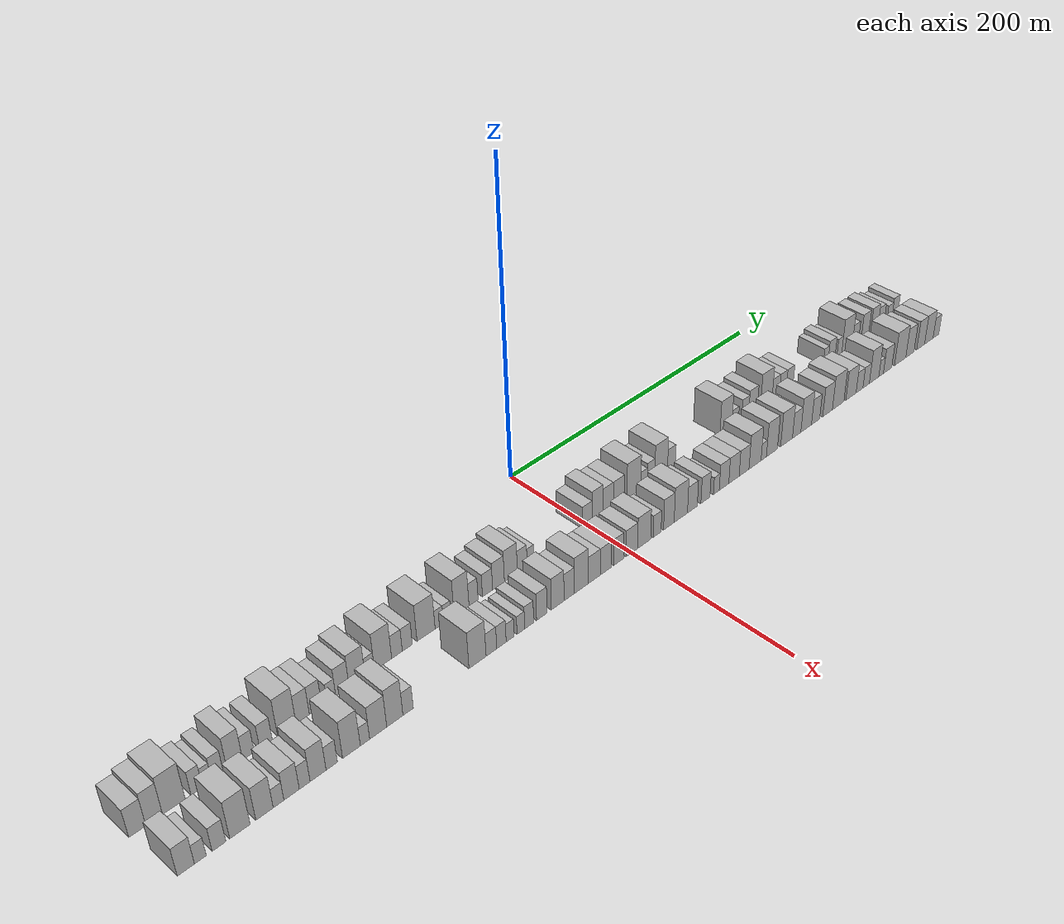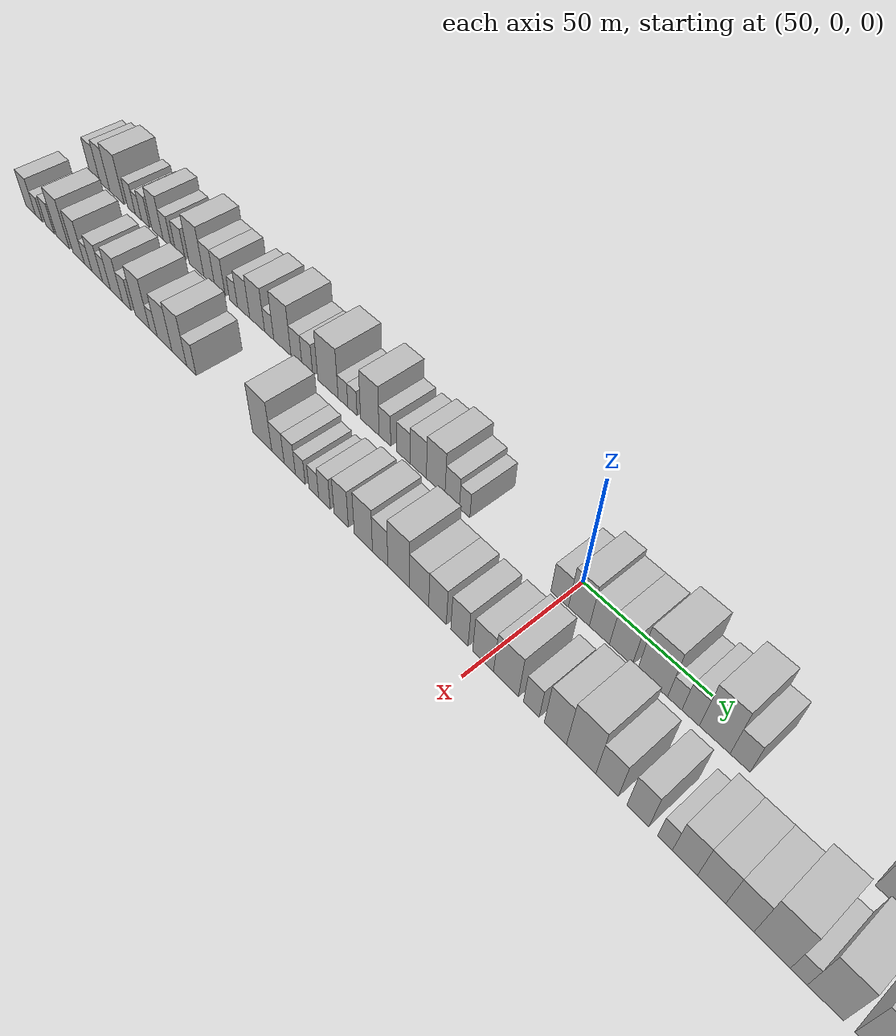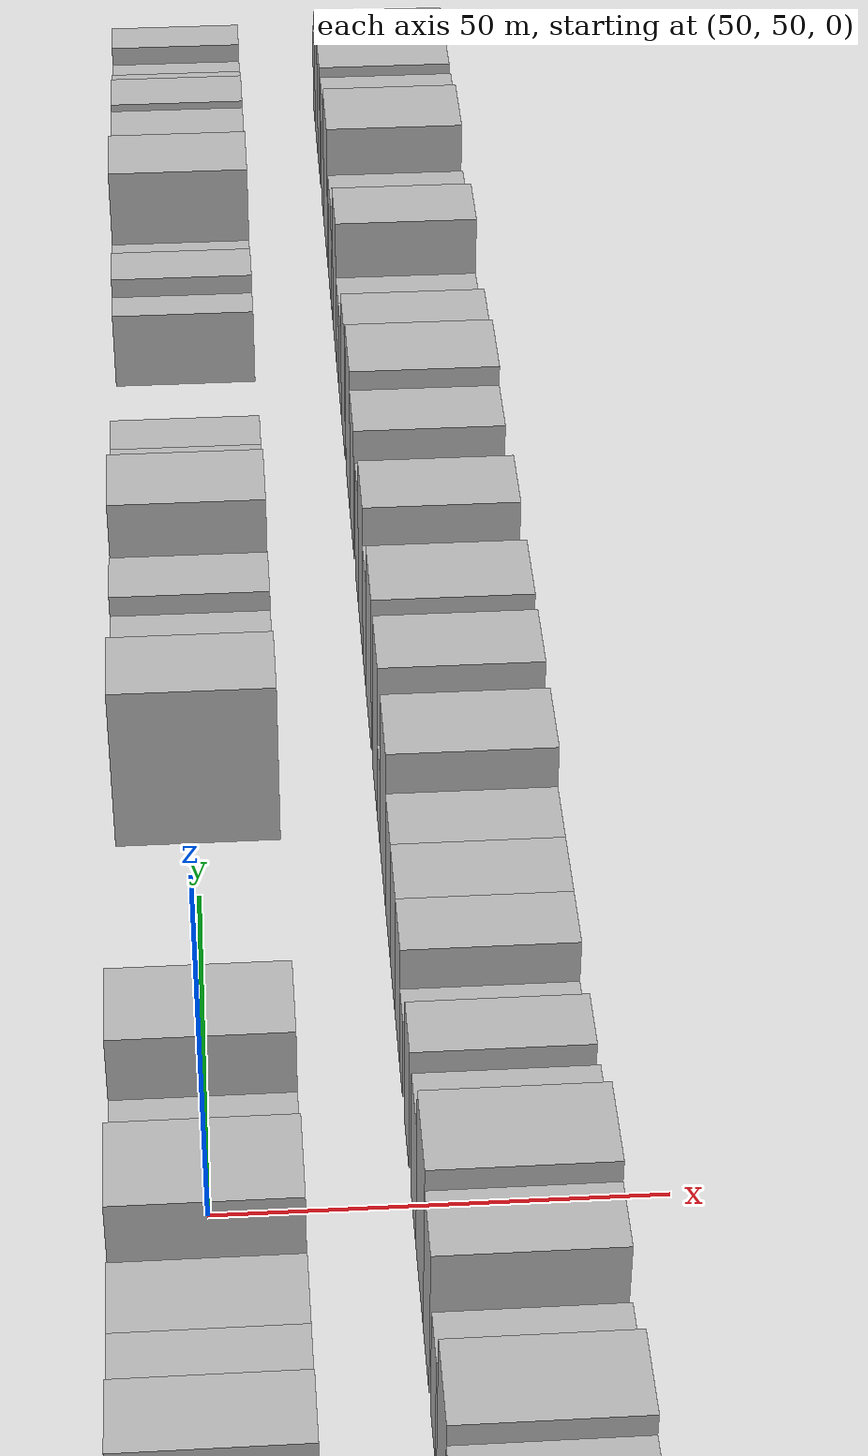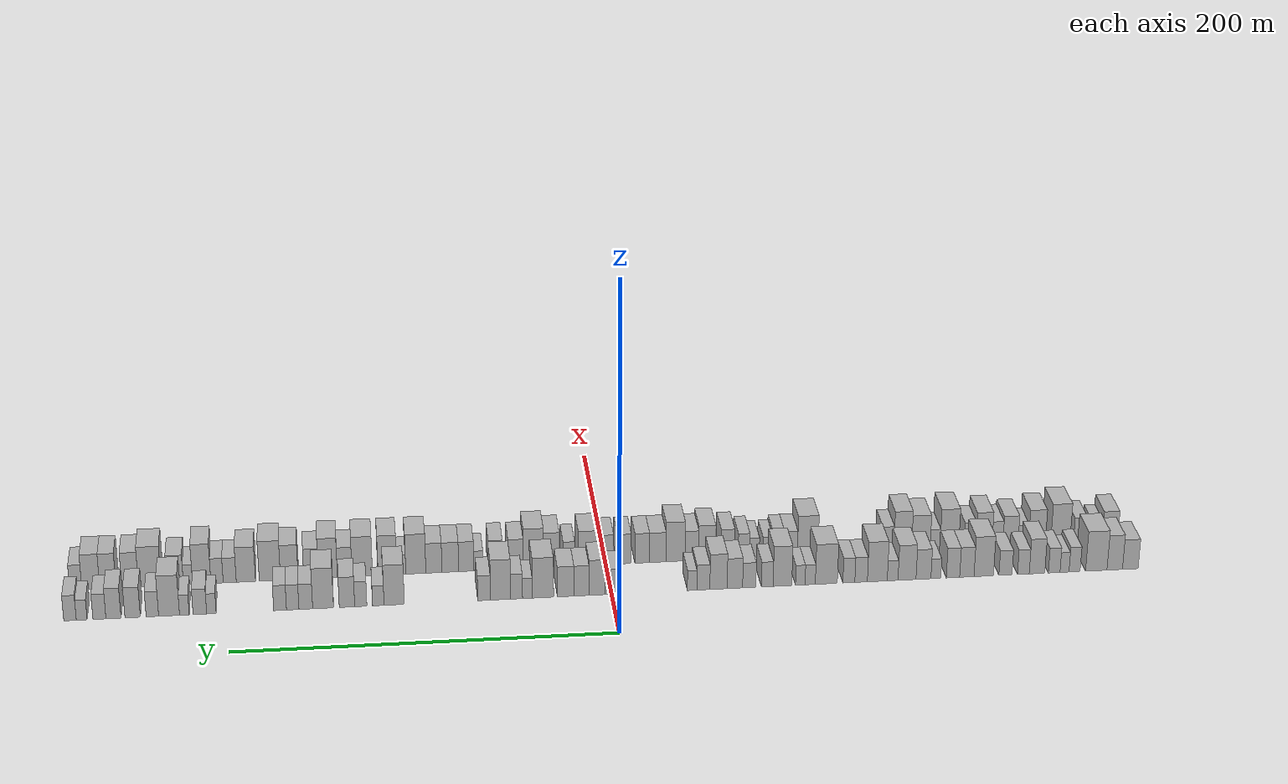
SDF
<sdf version="1.6">
 <world name="default">
  <scene>
   <sky><clouds><speed>12</speed></clouds></sky>
   <ambient>0.4 0.4 0.4 1</ambient>
   <background>0.7 0.7 0.7 1</background>
   <shadows>1</shadows>
  </scene>
  <gravity>0 0 -9.8066</gravity>
  <magnetic_field>6e-06 2.3e-05 -4.2e-05</magnetic_field>
  <physics default="0" name="default_physics" type="ode">
   <ode>
    <solver>
     <type>quick</type>
     <iters>10</iters>
     <sor>1.0</sor>
     <use_dynamic_moi_rescaling>0</use_dynamic_moi_rescaling>
    </solver>
    <constraints>
     <cfm>0</cfm>
     <erp>0.2</erp>
     <contact_max_correcting_vel>100</contact_max_correcting_vel>
     <contact_surface_layer>0.001</contact_surface_layer>
    </constraints>
   </ode>
   <max_step_size>0.004</max_step_size>
   <real_time_factor>1</real_time_factor>
   <real_time_update_rate>250</real_time_update_rate>
  </physics>
  <light name="sun" type="directional">
   <pose>0 0 10 0 0 0</pose>
   <diffuse>0.8 0.8 0.8 1</diffuse>
   <specular>0.2 0.2 0.2 1</specular>
   <attenuation>
    <range>1000</range>
    <constant>0.9</constant>
    <linear>0.01</linear>
    <quadratic>0.001</quadratic>
   </attenuation>
   <direction>-0.5 0.1 -0.9</direction>
  </light>
  <model name="building_1">
   <static>1</static>
   <pose>50.0000 -279.7125 0 0.000000 0.000000 0.000000</pose>
   <link name="link">
    <pose>0 0 9.00 0 0 0</pose>
    <collision name="collision"><geometry><box><size>20.0000 8.5751 18.0000</size></box></geometry></collision>
    <visual name="visual">
     <cast_shadows>0</cast_shadows>
     <geometry><box><size>20.0000 8.5751 18.0000</size></box></geometry>
     <material>
      <script>
       <uri>model://HANNAS_wall/materials/scripts</uri>
       <uri>model://HANNAS_wall/materials/textures</uri>
       <name>vrc/HANNAS_wall</name>
      </script>
     </material>
    </visual>
   </link>
  </model>
  <model name="building_2">
   <static>1</static>
   <pose>50.0000 -271.1900 0 0.000000 0.000000 0.000000</pose>
   <link name="link">
    <pose>0 0 10.50 0 0 0</pose>
    <collision name="collision"><geometry><box><size>20.0000 8.4698 21.0000</size></box></geometry></collision>
    <visual name="visual">
     <cast_shadows>0</cast_shadows>
     <geometry><box><size>20.0000 8.4698 21.0000</size></box></geometry>
     <material>
      <script>
       <uri>model://HANNAS_wall/materials/scripts</uri>
       <uri>model://HANNAS_wall/materials/textures</uri>
       <name>vrc/HANNAS_wall</name>
      </script>
     </material>
    </visual>
   </link>
  </model>
  <model name="building_3">
   <static>1</static>
   <pose>50.0000 -261.0978 0 0.000000 0.000000 0.000000</pose>
   <link name="link">
    <pose>0 0 12.00 0 0 0</pose>
    <collision name="collision"><geometry><box><size>20.0000 11.7146 24.0000</size></box></geometry></collision>
    <visual name="visual">
     <cast_shadows>0</cast_shadows>
     <geometry><box><size>20.0000 11.7146 24.0000</size></box></geometry>
     <material>
      <script>
       <uri>model://HANNAS_wall/materials/scripts</uri>
       <uri>model://HANNAS_wall/materials/textures</uri>
       <name>vrc/HANNAS_wall</name>
      </script>
     </material>
    </visual>
   </link>
  </model>
  <model name="building_4">
   <static>1</static>
   <pose>50.0000 -249.2100 0 0.000000 0.000000 0.000000</pose>
   <link name="link">
    <pose>0 0 7.50 0 0 0</pose>
    <collision name="collision"><geometry><box><size>20.0000 6.0610 15.0000</size></box></geometry></collision>
    <visual name="visual">
     <cast_shadows>0</cast_shadows>
     <geometry><box><size>20.0000 6.0610 15.0000</size></box></geometry>
     <material>
      <script>
       <uri>model://HANNAS_wall/materials/scripts</uri>
       <uri>model://HANNAS_wall/materials/textures</uri>
       <name>vrc/HANNAS_wall</name>
      </script>
     </material>
    </visual>
   </link>
  </model>
  <model name="building_5">
   <static>1</static>
   <pose>50.0000 -243.7288 0 0.000000 0.000000 0.000000</pose>
   <link name="link">
    <pose>0 0 6.00 0 0 0</pose>
    <collision name="collision"><geometry><box><size>20.0000 4.9014 12.0000</size></box></geometry></collision>
    <visual name="visual">
     <cast_shadows>0</cast_shadows>
     <geometry><box><size>20.0000 4.9014 12.0000</size></box></geometry>
     <material>
      <script>
       <uri>model://HANNAS_wall/materials/scripts</uri>
       <uri>model://HANNAS_wall/materials/textures</uri>
       <name>vrc/HANNAS_wall</name>
      </script>
     </material>
    </visual>
   </link>
  </model>
  <model name="building_6">
   <static>1</static>
   <pose>50.0000 -238.1100 0 0.000000 0.000000 0.000000</pose>
   <link name="link">
    <pose>0 0 7.50 0 0 0</pose>
    <collision name="collision"><geometry><box><size>20.0000 6.3363 15.0000</size></box></geometry></collision>
    <visual name="visual">
     <cast_shadows>0</cast_shadows>
     <geometry><box><size>20.0000 6.3363 15.0000</size></box></geometry>
     <material>
      <script>
       <uri>model://HANNAS_wall/materials/scripts</uri>
       <uri>model://HANNAS_wall/materials/textures</uri>
       <name>vrc/HANNAS_wall</name>
      </script>
     </material>
    </visual>
   </link>
  </model>
  <model name="building_7">
   <static>1</static>
   <pose>50.0000 -228.7135 0 0.000000 0.000000 0.000000</pose>
   <link name="link">
    <pose>0 0 10.50 0 0 0</pose>
    <collision name="collision"><geometry><box><size>20.0000 8.4566 21.0000</size></box></geometry></collision>
    <visual name="visual">
     <cast_shadows>0</cast_shadows>
     <geometry><box><size>20.0000 8.4566 21.0000</size></box></geometry>
     <material>
      <script>
       <uri>model://HANNAS_wall/materials/scripts</uri>
       <uri>model://HANNAS_wall/materials/textures</uri>
       <name>vrc/HANNAS_wall</name>
      </script>
     </material>
    </visual>
   </link>
  </model>
  <model name="building_8">
   <static>1</static>
   <pose>50.0000 -221.2973 0 0.000000 0.000000 0.000000</pose>
   <link name="link">
    <pose>0 0 7.50 0 0 0</pose>
    <collision name="collision"><geometry><box><size>20.0000 6.3758 15.0000</size></box></geometry></collision>
    <visual name="visual">
     <cast_shadows>0</cast_shadows>
     <geometry><box><size>20.0000 6.3758 15.0000</size></box></geometry>
     <material>
      <script>
       <uri>model://HANNAS_wall/materials/scripts</uri>
       <uri>model://HANNAS_wall/materials/textures</uri>
       <name>vrc/HANNAS_wall</name>
      </script>
     </material>
    </visual>
   </link>
  </model>
  <model name="building_9">
   <static>1</static>
   <pose>50.0000 -211.5569 0 0.000000 0.000000 0.000000</pose>
   <link name="link">
    <pose>0 0 7.50 0 0 0</pose>
    <collision name="collision"><geometry><box><size>20.0000 7.1049 15.0000</size></box></geometry></collision>
    <visual name="visual">
     <cast_shadows>0</cast_shadows>
     <geometry><box><size>20.0000 7.1049 15.0000</size></box></geometry>
     <material>
      <script>
       <uri>model://HANNAS_wall/materials/scripts</uri>
       <uri>model://HANNAS_wall/materials/textures</uri>
       <name>vrc/HANNAS_wall</name>
      </script>
     </material>
    </visual>
   </link>
  </model>
  <model name="building_10">
   <static>1</static>
   <pose>50.0000 -199.7303 0 0.000000 0.000000 0.000000</pose>
   <link name="link">
    <pose>0 0 12.00 0 0 0</pose>
    <collision name="collision"><geometry><box><size>20.0000 10.5482 24.0000</size></box></geometry></collision>
    <visual name="visual">
     <cast_shadows>0</cast_shadows>
     <geometry><box><size>20.0000 10.5482 24.0000</size></box></geometry>
     <material>
      <script>
       <uri>model://HANNAS_wall/materials/scripts</uri>
       <uri>model://HANNAS_wall/materials/textures</uri>
       <name>vrc/HANNAS_wall</name>
      </script>
     </material>
    </visual>
   </link>
  </model>
  <model name="building_11">
   <static>1</static>
   <pose>50.0000 -190.5804 0 0.000000 0.000000 0.000000</pose>
   <link name="link">
    <pose>0 0 9.00 0 0 0</pose>
    <collision name="collision"><geometry><box><size>20.0000 7.7517 18.0000</size></box></geometry></collision>
    <visual name="visual">
     <cast_shadows>0</cast_shadows>
     <geometry><box><size>20.0000 7.7517 18.0000</size></box></geometry>
     <material>
      <script>
       <uri>model://HANNAS_wall/materials/scripts</uri>
       <uri>model://HANNAS_wall/materials/textures</uri>
       <name>vrc/HANNAS_wall</name>
      </script>
     </material>
    </visual>
   </link>
  </model>
  <model name="building_12">
   <static>1</static>
   <pose>50.0000 -183.0801 0 0.000000 0.000000 0.000000</pose>
   <link name="link">
    <pose>0 0 9.00 0 0 0</pose>
    <collision name="collision"><geometry><box><size>20.0000 7.2488 18.0000</size></box></geometry></collision>
    <visual name="visual">
     <cast_shadows>0</cast_shadows>
     <geometry><box><size>20.0000 7.2488 18.0000</size></box></geometry>
     <material>
      <script>
       <uri>model://HANNAS_wall/materials/scripts</uri>
       <uri>model://HANNAS_wall/materials/textures</uri>
       <name>vrc/HANNAS_wall</name>
      </script>
     </material>
    </visual>
   </link>
  </model>
  <model name="building_13">
   <static>1</static>
   <pose>50.0000 -173.7837 0 0.000000 0.000000 0.000000</pose>
   <link name="link">
    <pose>0 0 6.00 0 0 0</pose>
    <collision name="collision"><geometry><box><size>20.0000 5.3440 12.0000</size></box></geometry></collision>
    <visual name="visual">
     <cast_shadows>0</cast_shadows>
     <geometry><box><size>20.0000 5.3440 12.0000</size></box></geometry>
     <material>
      <script>
       <uri>model://HANNAS_wall/materials/scripts</uri>
       <uri>model://HANNAS_wall/materials/textures</uri>
       <name>vrc/HANNAS_wall</name>
      </script>
     </material>
    </visual>
   </link>
  </model>
  <model name="building_14">
   <static>1</static>
   <pose>50.0000 -167.0755 0 0.000000 0.000000 0.000000</pose>
   <link name="link">
    <pose>0 0 9.00 0 0 0</pose>
    <collision name="collision"><geometry><box><size>20.0000 8.0723 18.0000</size></box></geometry></collision>
    <visual name="visual">
     <cast_shadows>0</cast_shadows>
     <geometry><box><size>20.0000 8.0723 18.0000</size></box></geometry>
     <material>
      <script>
       <uri>model://HANNAS_wall/materials/scripts</uri>
       <uri>model://HANNAS_wall/materials/textures</uri>
       <name>vrc/HANNAS_wall</name>
      </script>
     </material>
    </visual>
   </link>
  </model>
  <model name="building_15">
   <static>1</static>
   <pose>50.0000 -158.1807 0 0.000000 0.000000 0.000000</pose>
   <link name="link">
    <pose>0 0 10.50 0 0 0</pose>
    <collision name="collision"><geometry><box><size>20.0000 9.7175 21.0000</size></box></geometry></collision>
    <visual name="visual">
     <cast_shadows>0</cast_shadows>
     <geometry><box><size>20.0000 9.7175 21.0000</size></box></geometry>
     <material>
      <script>
       <uri>model://HANNAS_wall/materials/scripts</uri>
       <uri>model://HANNAS_wall/materials/textures</uri>
       <name>vrc/HANNAS_wall</name>
      </script>
     </material>
    </visual>
   </link>
  </model>
  <model name="building_16">
   <static>1</static>
   <pose>50.0000 -150.4176 0 0.000000 0.000000 0.000000</pose>
   <link name="link">
    <pose>0 0 6.00 0 0 0</pose>
    <collision name="collision"><geometry><box><size>20.0000 5.8087 12.0000</size></box></geometry></collision>
    <visual name="visual">
     <cast_shadows>0</cast_shadows>
     <geometry><box><size>20.0000 5.8087 12.0000</size></box></geometry>
     <material>
      <script>
       <uri>model://HANNAS_wall/materials/scripts</uri>
       <uri>model://HANNAS_wall/materials/textures</uri>
       <name>vrc/HANNAS_wall</name>
      </script>
     </material>
    </visual>
   </link>
  </model>
  <model name="building_17">
   <static>1</static>
   <pose>50.0000 -142.1498 0 0.000000 0.000000 0.000000</pose>
   <link name="link">
    <pose>0 0 12.00 0 0 0</pose>
    <collision name="collision"><geometry><box><size>20.0000 10.7268 24.0000</size></box></geometry></collision>
    <visual name="visual">
     <cast_shadows>0</cast_shadows>
     <geometry><box><size>20.0000 10.7268 24.0000</size></box></geometry>
     <material>
      <script>
       <uri>model://HANNAS_wall/materials/scripts</uri>
       <uri>model://HANNAS_wall/materials/textures</uri>
       <name>vrc/HANNAS_wall</name>
      </script>
     </material>
    </visual>
   </link>
  </model>
  <model name="building_18">
   <static>1</static>
   <pose>50.0000 -133.4117 0 0.000000 0.000000 0.000000</pose>
   <link name="link">
    <pose>0 0 7.50 0 0 0</pose>
    <collision name="collision"><geometry><box><size>20.0000 6.7494 15.0000</size></box></geometry></collision>
    <visual name="visual">
     <cast_shadows>0</cast_shadows>
     <geometry><box><size>20.0000 6.7494 15.0000</size></box></geometry>
     <material>
      <script>
       <uri>model://HANNAS_wall/materials/scripts</uri>
       <uri>model://HANNAS_wall/materials/textures</uri>
       <name>vrc/HANNAS_wall</name>
      </script>
     </material>
    </visual>
   </link>
  </model>
  <model name="building_19">
   <static>1</static>
   <pose>50.0000 -126.8120 0 0.000000 0.000000 0.000000</pose>
   <link name="link">
    <pose>0 0 7.50 0 0 0</pose>
    <collision name="collision"><geometry><box><size>20.0000 6.4500 15.0000</size></box></geometry></collision>
    <visual name="visual">
     <cast_shadows>0</cast_shadows>
     <geometry><box><size>20.0000 6.4500 15.0000</size></box></geometry>
     <material>
      <script>
       <uri>model://HANNAS_wall/materials/scripts</uri>
       <uri>model://HANNAS_wall/materials/textures</uri>
       <name>vrc/HANNAS_wall</name>
      </script>
     </material>
    </visual>
   </link>
  </model>
  <model name="building_20">
   <static>1</static>
   <pose>50.0000 -114.6766 0 0.000000 0.000000 0.000000</pose>
   <link name="link">
    <pose>0 0 12.00 0 0 0</pose>
    <collision name="collision"><geometry><box><size>20.0000 11.8208 24.0000</size></box></geometry></collision>
    <visual name="visual">
     <cast_shadows>0</cast_shadows>
     <geometry><box><size>20.0000 11.8208 24.0000</size></box></geometry>
     <material>
      <script>
       <uri>model://HANNAS_wall/materials/scripts</uri>
       <uri>model://HANNAS_wall/materials/textures</uri>
       <name>vrc/HANNAS_wall</name>
      </script>
     </material>
    </visual>
   </link>
  </model>
  <model name="building_21">
   <static>1</static>
   <pose>50.0000 -106.0119 0 0.000000 0.000000 0.000000</pose>
   <link name="link">
    <pose>0 0 6.00 0 0 0</pose>
    <collision name="collision"><geometry><box><size>20.0000 5.5086 12.0000</size></box></geometry></collision>
    <visual name="visual">
     <cast_shadows>0</cast_shadows>
     <geometry><box><size>20.0000 5.5086 12.0000</size></box></geometry>
     <material>
      <script>
       <uri>model://HANNAS_wall/materials/scripts</uri>
       <uri>model://HANNAS_wall/materials/textures</uri>
       <name>vrc/HANNAS_wall</name>
      </script>
     </material>
    </visual>
   </link>
  </model>
  <model name="building_22">
   <static>1</static>
   <pose>50.0000 -100.6855 0 0.000000 0.000000 0.000000</pose>
   <link name="link">
    <pose>0 0 6.00 0 0 0</pose>
    <collision name="collision"><geometry><box><size>20.0000 5.1442 12.0000</size></box></geometry></collision>
    <visual name="visual">
     <cast_shadows>0</cast_shadows>
     <geometry><box><size>20.0000 5.1442 12.0000</size></box></geometry>
     <material>
      <script>
       <uri>model://HANNAS_wall/materials/scripts</uri>
       <uri>model://HANNAS_wall/materials/textures</uri>
       <name>vrc/HANNAS_wall</name>
      </script>
     </material>
    </visual>
   </link>
  </model>
  <model name="building_23">
   <static>1</static>
   <pose>50.0000 -91.1002 0 0.000000 0.000000 0.000000</pose>
   <link name="link">
    <pose>0 0 12.00 0 0 0</pose>
    <collision name="collision"><geometry><box><size>20.0000 10.0264 24.0000</size></box></geometry></collision>
    <visual name="visual">
     <cast_shadows>0</cast_shadows>
     <geometry><box><size>20.0000 10.0264 24.0000</size></box></geometry>
     <material>
      <script>
       <uri>model://HANNAS_wall/materials/scripts</uri>
       <uri>model://HANNAS_wall/materials/textures</uri>
       <name>vrc/HANNAS_wall</name>
      </script>
     </material>
    </visual>
   </link>
  </model>
  <model name="building_24">
   <static>1</static>
   <pose>50.0000 -82.9708 0 0.000000 0.000000 0.000000</pose>
   <link name="link">
    <pose>0 0 7.50 0 0 0</pose>
    <collision name="collision"><geometry><box><size>20.0000 6.2323 15.0000</size></box></geometry></collision>
    <visual name="visual">
     <cast_shadows>0</cast_shadows>
     <geometry><box><size>20.0000 6.2323 15.0000</size></box></geometry>
     <material>
      <script>
       <uri>model://HANNAS_wall/materials/scripts</uri>
       <uri>model://HANNAS_wall/materials/textures</uri>
       <name>vrc/HANNAS_wall</name>
      </script>
     </material>
    </visual>
   </link>
  </model>
  <model name="building_25">
   <static>1</static>
   <pose>50.0000 -73.3102 0 0.000000 0.000000 0.000000</pose>
   <link name="link">
    <pose>0 0 7.50 0 0 0</pose>
    <collision name="collision"><geometry><box><size>20.0000 7.0889 15.0000</size></box></geometry></collision>
    <visual name="visual">
     <cast_shadows>0</cast_shadows>
     <geometry><box><size>20.0000 7.0889 15.0000</size></box></geometry>
     <material>
      <script>
       <uri>model://HANNAS_wall/materials/scripts</uri>
       <uri>model://HANNAS_wall/materials/textures</uri>
       <name>vrc/HANNAS_wall</name>
      </script>
     </material>
    </visual>
   </link>
  </model>
  <model name="building_26">
   <static>1</static>
   <pose>50.0000 -65.6326 0 0.000000 0.000000 0.000000</pose>
   <link name="link">
    <pose>0 0 9.00 0 0 0</pose>
    <collision name="collision"><geometry><box><size>20.0000 8.2663 18.0000</size></box></geometry></collision>
    <visual name="visual">
     <cast_shadows>0</cast_shadows>
     <geometry><box><size>20.0000 8.2663 18.0000</size></box></geometry>
     <material>
      <script>
       <uri>model://HANNAS_wall/materials/scripts</uri>
       <uri>model://HANNAS_wall/materials/textures</uri>
       <name>vrc/HANNAS_wall</name>
      </script>
     </material>
    </visual>
   </link>
  </model>
  <model name="building_27">
   <static>1</static>
   <pose>50.0000 -56.8797 0 0.000000 0.000000 0.000000</pose>
   <link name="link">
    <pose>0 0 10.50 0 0 0</pose>
    <collision name="collision"><geometry><box><size>20.0000 9.2396 21.0000</size></box></geometry></collision>
    <visual name="visual">
     <cast_shadows>0</cast_shadows>
     <geometry><box><size>20.0000 9.2396 21.0000</size></box></geometry>
     <material>
      <script>
       <uri>model://HANNAS_wall/materials/scripts</uri>
       <uri>model://HANNAS_wall/materials/textures</uri>
       <name>vrc/HANNAS_wall</name>
      </script>
     </material>
    </visual>
   </link>
  </model>
  <model name="building_28">
   <static>1</static>
   <pose>50.0000 -48.7602 0 0.000000 0.000000 0.000000</pose>
   <link name="link">
    <pose>0 0 7.50 0 0 0</pose>
    <collision name="collision"><geometry><box><size>20.0000 6.9993 15.0000</size></box></geometry></collision>
    <visual name="visual">
     <cast_shadows>0</cast_shadows>
     <geometry><box><size>20.0000 6.9993 15.0000</size></box></geometry>
     <material>
      <script>
       <uri>model://HANNAS_wall/materials/scripts</uri>
       <uri>model://HANNAS_wall/materials/textures</uri>
       <name>vrc/HANNAS_wall</name>
      </script>
     </material>
    </visual>
   </link>
  </model>
  <model name="building_29">
   <static>1</static>
   <pose>50.0000 -42.7589 0 0.000000 0.000000 0.000000</pose>
   <link name="link">
    <pose>0 0 6.00 0 0 0</pose>
    <collision name="collision"><geometry><box><size>20.0000 5.0032 12.0000</size></box></geometry></collision>
    <visual name="visual">
     <cast_shadows>0</cast_shadows>
     <geometry><box><size>20.0000 5.0032 12.0000</size></box></geometry>
     <material>
      <script>
       <uri>model://HANNAS_wall/materials/scripts</uri>
       <uri>model://HANNAS_wall/materials/textures</uri>
       <name>vrc/HANNAS_wall</name>
      </script>
     </material>
    </visual>
   </link>
  </model>
  <model name="building_30">
   <static>1</static>
   <pose>50.0000 -0.2794 0 0.000000 0.000000 0.000000</pose>
   <link name="link">
    <pose>0 0 7.50 0 0 0</pose>
    <collision name="collision"><geometry><box><size>20.0000 7.3186 15.0000</size></box></geometry></collision>
    <visual name="visual">
     <cast_shadows>0</cast_shadows>
     <geometry><box><size>20.0000 7.3186 15.0000</size></box></geometry>
     <material>
      <script>
       <uri>model://HANNAS_wall/materials/scripts</uri>
       <uri>model://HANNAS_wall/materials/textures</uri>
       <name>vrc/HANNAS_wall</name>
      </script>
     </material>
    </visual>
   </link>
  </model>
  <model name="building_31">
   <static>1</static>
   <pose>50.0000 7.6886 0 0.000000 0.000000 0.000000</pose>
   <link name="link">
    <pose>0 0 10.50 0 0 0</pose>
    <collision name="collision"><geometry><box><size>20.0000 8.6175 21.0000</size></box></geometry></collision>
    <visual name="visual">
     <cast_shadows>0</cast_shadows>
     <geometry><box><size>20.0000 8.6175 21.0000</size></box></geometry>
     <material>
      <script>
       <uri>model://HANNAS_wall/materials/scripts</uri>
       <uri>model://HANNAS_wall/materials/textures</uri>
       <name>vrc/HANNAS_wall</name>
      </script>
     </material>
    </visual>
   </link>
  </model>
  <model name="building_32">
   <static>1</static>
   <pose>50.0000 15.9778 0 0.000000 0.000000 0.000000</pose>
   <link name="link">
    <pose>0 0 9.00 0 0 0</pose>
    <collision name="collision"><geometry><box><size>20.0000 7.9609 18.0000</size></box></geometry></collision>
    <visual name="visual">
     <cast_shadows>0</cast_shadows>
     <geometry><box><size>20.0000 7.9609 18.0000</size></box></geometry>
     <material>
      <script>
       <uri>model://HANNAS_wall/materials/scripts</uri>
       <uri>model://HANNAS_wall/materials/textures</uri>
       <name>vrc/HANNAS_wall</name>
      </script>
     </material>
    </visual>
   </link>
  </model>
  <model name="building_33">
   <static>1</static>
   <pose>50.0000 24.3910 0 0.000000 0.000000 0.000000</pose>
   <link name="link">
    <pose>0 0 9.00 0 0 0</pose>
    <collision name="collision"><geometry><box><size>20.0000 8.8656 18.0000</size></box></geometry></collision>
    <visual name="visual">
     <cast_shadows>0</cast_shadows>
     <geometry><box><size>20.0000 8.8656 18.0000</size></box></geometry>
     <material>
      <script>
       <uri>model://HANNAS_wall/materials/scripts</uri>
       <uri>model://HANNAS_wall/materials/textures</uri>
       <name>vrc/HANNAS_wall</name>
      </script>
     </material>
    </visual>
   </link>
  </model>
  <model name="building_34">
   <static>1</static>
   <pose>50.0000 36.4261 0 0.000000 0.000000 0.000000</pose>
   <link name="link">
    <pose>0 0 12.00 0 0 0</pose>
    <collision name="collision"><geometry><box><size>20.0000 11.2045 24.0000</size></box></geometry></collision>
    <visual name="visual">
     <cast_shadows>0</cast_shadows>
     <geometry><box><size>20.0000 11.2045 24.0000</size></box></geometry>
     <material>
      <script>
       <uri>model://HANNAS_wall/materials/scripts</uri>
       <uri>model://HANNAS_wall/materials/textures</uri>
       <name>vrc/HANNAS_wall</name>
      </script>
     </material>
    </visual>
   </link>
  </model>
  <model name="building_35">
   <static>1</static>
   <pose>50.0000 44.6338 0 0.000000 0.000000 0.000000</pose>
   <link name="link">
    <pose>0 0 6.00 0 0 0</pose>
    <collision name="collision"><geometry><box><size>20.0000 5.2108 12.0000</size></box></geometry></collision>
    <visual name="visual">
     <cast_shadows>0</cast_shadows>
     <geometry><box><size>20.0000 5.2108 12.0000</size></box></geometry>
     <material>
      <script>
       <uri>model://HANNAS_wall/materials/scripts</uri>
       <uri>model://HANNAS_wall/materials/textures</uri>
       <name>vrc/HANNAS_wall</name>
      </script>
     </material>
    </visual>
   </link>
  </model>
  <model name="building_36">
   <static>1</static>
   <pose>50.0000 50.3678 0 0.000000 0.000000 0.000000</pose>
   <link name="link">
    <pose>0 0 7.50 0 0 0</pose>
    <collision name="collision"><geometry><box><size>20.0000 6.2572 15.0000</size></box></geometry></collision>
    <visual name="visual">
     <cast_shadows>0</cast_shadows>
     <geometry><box><size>20.0000 6.2572 15.0000</size></box></geometry>
     <material>
      <script>
       <uri>model://HANNAS_wall/materials/scripts</uri>
       <uri>model://HANNAS_wall/materials/textures</uri>
       <name>vrc/HANNAS_wall</name>
      </script>
     </material>
    </visual>
   </link>
  </model>
  <model name="building_37">
   <static>1</static>
   <pose>50.0000 58.8005 0 0.000000 0.000000 0.000000</pose>
   <link name="link">
    <pose>0 0 12.00 0 0 0</pose>
    <collision name="collision"><geometry><box><size>20.0000 10.6083 24.0000</size></box></geometry></collision>
    <visual name="visual">
     <cast_shadows>0</cast_shadows>
     <geometry><box><size>20.0000 10.6083 24.0000</size></box></geometry>
     <material>
      <script>
       <uri>model://HANNAS_wall/materials/scripts</uri>
       <uri>model://HANNAS_wall/materials/textures</uri>
       <name>vrc/HANNAS_wall</name>
      </script>
     </material>
    </visual>
   </link>
  </model>
  <model name="building_38">
   <static>1</static>
   <pose>50.0000 67.4824 0 0.000000 0.000000 0.000000</pose>
   <link name="link">
    <pose>0 0 7.50 0 0 0</pose>
    <collision name="collision"><geometry><box><size>20.0000 6.7556 15.0000</size></box></geometry></collision>
    <visual name="visual">
     <cast_shadows>0</cast_shadows>
     <geometry><box><size>20.0000 6.7556 15.0000</size></box></geometry>
     <material>
      <script>
       <uri>model://HANNAS_wall/materials/scripts</uri>
       <uri>model://HANNAS_wall/materials/textures</uri>
       <name>vrc/HANNAS_wall</name>
      </script>
     </material>
    </visual>
   </link>
  </model>
  <model name="building_39">
   <static>1</static>
   <pose>50.0000 114.7980 0 0.000000 0.000000 0.000000</pose>
   <link name="link">
    <pose>0 0 12.00 0 0 0</pose>
    <collision name="collision"><geometry><box><size>20.0000 10.6252 24.0000</size></box></geometry></collision>
    <visual name="visual">
     <cast_shadows>0</cast_shadows>
     <geometry><box><size>20.0000 10.6252 24.0000</size></box></geometry>
     <material>
      <script>
       <uri>model://HANNAS_wall/materials/scripts</uri>
       <uri>model://HANNAS_wall/materials/textures</uri>
       <name>vrc/HANNAS_wall</name>
      </script>
     </material>
    </visual>
   </link>
  </model>
  <model name="building_40">
   <static>1</static>
   <pose>50.0000 123.1017 0 0.000000 0.000000 0.000000</pose>
   <link name="link">
    <pose>0 0 6.00 0 0 0</pose>
    <collision name="collision"><geometry><box><size>20.0000 5.9823 12.0000</size></box></geometry></collision>
    <visual name="visual">
     <cast_shadows>0</cast_shadows>
     <geometry><box><size>20.0000 5.9823 12.0000</size></box></geometry>
     <material>
      <script>
       <uri>model://HANNAS_wall/materials/scripts</uri>
       <uri>model://HANNAS_wall/materials/textures</uri>
       <name>vrc/HANNAS_wall</name>
      </script>
     </material>
    </visual>
   </link>
  </model>
  <model name="building_41">
   <static>1</static>
   <pose>50.0000 132.2804 0 0.000000 0.000000 0.000000</pose>
   <link name="link">
    <pose>0 0 7.50 0 0 0</pose>
    <collision name="collision"><geometry><box><size>20.0000 6.3750 15.0000</size></box></geometry></collision>
    <visual name="visual">
     <cast_shadows>0</cast_shadows>
     <geometry><box><size>20.0000 6.3750 15.0000</size></box></geometry>
     <material>
      <script>
       <uri>model://HANNAS_wall/materials/scripts</uri>
       <uri>model://HANNAS_wall/materials/textures</uri>
       <name>vrc/HANNAS_wall</name>
      </script>
     </material>
    </visual>
   </link>
  </model>
  <model name="building_42">
   <static>1</static>
   <pose>50.0000 139.5028 0 0.000000 0.000000 0.000000</pose>
   <link name="link">
    <pose>0 0 9.00 0 0 0</pose>
    <collision name="collision"><geometry><box><size>20.0000 8.0697 18.0000</size></box></geometry></collision>
    <visual name="visual">
     <cast_shadows>0</cast_shadows>
     <geometry><box><size>20.0000 8.0697 18.0000</size></box></geometry>
     <material>
      <script>
       <uri>model://HANNAS_wall/materials/scripts</uri>
       <uri>model://HANNAS_wall/materials/textures</uri>
       <name>vrc/HANNAS_wall</name>
      </script>
     </material>
    </visual>
   </link>
  </model>
  <model name="building_43">
   <static>1</static>
   <pose>50.0000 151.9790 0 0.000000 0.000000 0.000000</pose>
   <link name="link">
    <pose>0 0 12.00 0 0 0</pose>
    <collision name="collision"><geometry><box><size>20.0000 10.8826 24.0000</size></box></geometry></collision>
    <visual name="visual">
     <cast_shadows>0</cast_shadows>
     <geometry><box><size>20.0000 10.8826 24.0000</size></box></geometry>
     <material>
      <script>
       <uri>model://HANNAS_wall/materials/scripts</uri>
       <uri>model://HANNAS_wall/materials/textures</uri>
       <name>vrc/HANNAS_wall</name>
      </script>
     </material>
    </visual>
   </link>
  </model>
  <model name="building_44">
   <static>1</static>
   <pose>50.0000 161.0031 0 0.000000 0.000000 0.000000</pose>
   <link name="link">
    <pose>0 0 7.50 0 0 0</pose>
    <collision name="collision"><geometry><box><size>20.0000 7.1656 15.0000</size></box></geometry></collision>
    <visual name="visual">
     <cast_shadows>0</cast_shadows>
     <geometry><box><size>20.0000 7.1656 15.0000</size></box></geometry>
     <material>
      <script>
       <uri>model://HANNAS_wall/materials/scripts</uri>
       <uri>model://HANNAS_wall/materials/textures</uri>
       <name>vrc/HANNAS_wall</name>
      </script>
     </material>
    </visual>
   </link>
  </model>
  <model name="building_45">
   <static>1</static>
   <pose>50.0000 167.8345 0 0.000000 0.000000 0.000000</pose>
   <link name="link">
    <pose>0 0 7.50 0 0 0</pose>
    <collision name="collision"><geometry><box><size>20.0000 6.4972 15.0000</size></box></geometry></collision>
    <visual name="visual">
     <cast_shadows>0</cast_shadows>
     <geometry><box><size>20.0000 6.4972 15.0000</size></box></geometry>
     <material>
      <script>
       <uri>model://HANNAS_wall/materials/scripts</uri>
       <uri>model://HANNAS_wall/materials/textures</uri>
       <name>vrc/HANNAS_wall</name>
      </script>
     </material>
    </visual>
   </link>
  </model>
  <model name="building_46">
   <static>1</static>
   <pose>50.0000 174.4010 0 0.000000 0.000000 0.000000</pose>
   <link name="link">
    <pose>0 0 7.50 0 0 0</pose>
    <collision name="collision"><geometry><box><size>20.0000 6.6358 15.0000</size></box></geometry></collision>
    <visual name="visual">
     <cast_shadows>0</cast_shadows>
     <geometry><box><size>20.0000 6.6358 15.0000</size></box></geometry>
     <material>
      <script>
       <uri>model://HANNAS_wall/materials/scripts</uri>
       <uri>model://HANNAS_wall/materials/textures</uri>
       <name>vrc/HANNAS_wall</name>
      </script>
     </material>
    </visual>
   </link>
  </model>
  <model name="building_47">
   <static>1</static>
   <pose>50.0000 210.0900 0 0.000000 0.000000 0.000000</pose>
   <link name="link">
    <pose>0 0 6.00 0 0 0</pose>
    <collision name="collision"><geometry><box><size>20.0000 4.9141 12.0000</size></box></geometry></collision>
    <visual name="visual">
     <cast_shadows>0</cast_shadows>
     <geometry><box><size>20.0000 4.9141 12.0000</size></box></geometry>
     <material>
      <script>
       <uri>model://HANNAS_wall/materials/scripts</uri>
       <uri>model://HANNAS_wall/materials/textures</uri>
       <name>vrc/HANNAS_wall</name>
      </script>
     </material>
    </visual>
   </link>
  </model>
  <model name="building_48">
   <static>1</static>
   <pose>50.0000 216.0819 0 0.000000 0.000000 0.000000</pose>
   <link name="link">
    <pose>0 0 7.50 0 0 0</pose>
    <collision name="collision"><geometry><box><size>20.0000 7.0696 15.0000</size></box></geometry></collision>
    <visual name="visual">
     <cast_shadows>0</cast_shadows>
     <geometry><box><size>20.0000 7.0696 15.0000</size></box></geometry>
     <material>
      <script>
       <uri>model://HANNAS_wall/materials/scripts</uri>
       <uri>model://HANNAS_wall/materials/textures</uri>
       <name>vrc/HANNAS_wall</name>
      </script>
     </material>
    </visual>
   </link>
  </model>
  <model name="building_49">
   <static>1</static>
   <pose>50.0000 224.1275 0 0.000000 0.000000 0.000000</pose>
   <link name="link">
    <pose>0 0 6.00 0 0 0</pose>
    <collision name="collision"><geometry><box><size>20.0000 5.0218 12.0000</size></box></geometry></collision>
    <visual name="visual">
     <cast_shadows>0</cast_shadows>
     <geometry><box><size>20.0000 5.0218 12.0000</size></box></geometry>
     <material>
      <script>
       <uri>model://HANNAS_wall/materials/scripts</uri>
       <uri>model://HANNAS_wall/materials/textures</uri>
       <name>vrc/HANNAS_wall</name>
      </script>
     </material>
    </visual>
   </link>
  </model>
  <model name="building_50">
   <static>1</static>
   <pose>50.0000 232.0344 0 0.000000 0.000000 0.000000</pose>
   <link name="link">
    <pose>0 0 12.00 0 0 0</pose>
    <collision name="collision"><geometry><box><size>20.0000 10.7920 24.0000</size></box></geometry></collision>
    <visual name="visual">
     <cast_shadows>0</cast_shadows>
     <geometry><box><size>20.0000 10.7920 24.0000</size></box></geometry>
     <material>
      <script>
       <uri>model://HANNAS_wall/materials/scripts</uri>
       <uri>model://HANNAS_wall/materials/textures</uri>
       <name>vrc/HANNAS_wall</name>
      </script>
     </material>
    </visual>
   </link>
  </model>
  <model name="building_51">
   <static>1</static>
   <pose>50.0000 240.6646 0 0.000000 0.000000 0.000000</pose>
   <link name="link">
    <pose>0 0 7.50 0 0 0</pose>
    <collision name="collision"><geometry><box><size>20.0000 6.4684 15.0000</size></box></geometry></collision>
    <visual name="visual">
     <cast_shadows>0</cast_shadows>
     <geometry><box><size>20.0000 6.4684 15.0000</size></box></geometry>
     <material>
      <script>
       <uri>model://HANNAS_wall/materials/scripts</uri>
       <uri>model://HANNAS_wall/materials/textures</uri>
       <name>vrc/HANNAS_wall</name>
      </script>
     </material>
    </visual>
   </link>
  </model>
  <model name="building_52">
   <static>1</static>
   <pose>50.0000 250.8795 0 0.000000 0.000000 0.000000</pose>
   <link name="link">
    <pose>0 0 9.00 0 0 0</pose>
    <collision name="collision"><geometry><box><size>20.0000 7.9615 18.0000</size></box></geometry></collision>
    <visual name="visual">
     <cast_shadows>0</cast_shadows>
     <geometry><box><size>20.0000 7.9615 18.0000</size></box></geometry>
     <material>
      <script>
       <uri>model://HANNAS_wall/materials/scripts</uri>
       <uri>model://HANNAS_wall/materials/textures</uri>
       <name>vrc/HANNAS_wall</name>
      </script>
     </material>
    </visual>
   </link>
  </model>
  <model name="building_53">
   <static>1</static>
   <pose>50.0000 260.7514 0 0.000000 0.000000 0.000000</pose>
   <link name="link">
    <pose>0 0 9.00 0 0 0</pose>
    <collision name="collision"><geometry><box><size>20.0000 7.7824 18.0000</size></box></geometry></collision>
    <visual name="visual">
     <cast_shadows>0</cast_shadows>
     <geometry><box><size>20.0000 7.7824 18.0000</size></box></geometry>
     <material>
      <script>
       <uri>model://HANNAS_wall/materials/scripts</uri>
       <uri>model://HANNAS_wall/materials/textures</uri>
       <name>vrc/HANNAS_wall</name>
      </script>
     </material>
    </visual>
   </link>
  </model>
  <model name="building_54">
   <static>1</static>
   <pose>50.0000 267.9946 0 0.000000 0.000000 0.000000</pose>
   <link name="link">
    <pose>0 0 7.50 0 0 0</pose>
    <collision name="collision"><geometry><box><size>20.0000 6.7040 15.0000</size></box></geometry></collision>
    <visual name="visual">
     <cast_shadows>0</cast_shadows>
     <geometry><box><size>20.0000 6.7040 15.0000</size></box></geometry>
     <material>
      <script>
       <uri>model://HANNAS_wall/materials/scripts</uri>
       <uri>model://HANNAS_wall/materials/textures</uri>
       <name>vrc/HANNAS_wall</name>
      </script>
     </material>
    </visual>
   </link>
  </model>
  <model name="building_55">
   <static>1</static>
   <pose>50.0000 277.1277 0 0.000000 0.000000 0.000000</pose>
   <link name="link">
    <pose>0 0 6.00 0 0 0</pose>
    <collision name="collision"><geometry><box><size>20.0000 5.5620 12.0000</size></box></geometry></collision>
    <visual name="visual">
     <cast_shadows>0</cast_shadows>
     <geometry><box><size>20.0000 5.5620 12.0000</size></box></geometry>
     <material>
      <script>
       <uri>model://HANNAS_wall/materials/scripts</uri>
       <uri>model://HANNAS_wall/materials/textures</uri>
       <name>vrc/HANNAS_wall</name>
      </script>
     </material>
    </visual>
   </link>
  </model>
  <model name="building_56">
   <static>1</static>
   <pose>50.0000 283.1235 0 0.000000 0.000000 0.000000</pose>
   <link name="link">
    <pose>0 0 7.50 0 0 0</pose>
    <collision name="collision"><geometry><box><size>20.0000 6.4297 15.0000</size></box></geometry></collision>
    <visual name="visual">
     <cast_shadows>0</cast_shadows>
     <geometry><box><size>20.0000 6.4297 15.0000</size></box></geometry>
     <material>
      <script>
       <uri>model://HANNAS_wall/materials/scripts</uri>
       <uri>model://HANNAS_wall/materials/textures</uri>
       <name>vrc/HANNAS_wall</name>
      </script>
     </material>
    </visual>
   </link>
  </model>
  <model name="building_57">
   <static>1</static>
   <pose>82.0000 -276.6978 0 0.000000 0.000000 0.000000</pose>
   <link name="link">
    <pose>0 0 9.00 0 0 0</pose>
    <collision name="collision"><geometry><box><size>20.0000 8.6043 18.0000</size></box></geometry></collision>
    <visual name="visual">
     <cast_shadows>0</cast_shadows>
     <geometry><box><size>20.0000 8.6043 18.0000</size></box></geometry>
     <material>
      <script>
       <uri>model://HANNAS_wall/materials/scripts</uri>
       <uri>model://HANNAS_wall/materials/textures</uri>
       <name>vrc/HANNAS_wall</name>
      </script>
     </material>
    </visual>
   </link>
  </model>
  <model name="building_58">
   <static>1</static>
   <pose>82.0000 -269.4161 0 0.000000 0.000000 0.000000</pose>
   <link name="link">
    <pose>0 0 6.00 0 0 0</pose>
    <collision name="collision"><geometry><box><size>20.0000 5.9592 12.0000</size></box></geometry></collision>
    <visual name="visual">
     <cast_shadows>0</cast_shadows>
     <geometry><box><size>20.0000 5.9592 12.0000</size></box></geometry>
     <material>
      <script>
       <uri>model://HANNAS_wall/materials/scripts</uri>
       <uri>model://HANNAS_wall/materials/textures</uri>
       <name>vrc/HANNAS_wall</name>
      </script>
     </material>
    </visual>
   </link>
  </model>
  <model name="building_59">
   <static>1</static>
   <pose>82.0000 -259.9107 0 0.000000 0.000000 0.000000</pose>
   <link name="link">
    <pose>0 0 7.50 0 0 0</pose>
    <collision name="collision"><geometry><box><size>20.0000 7.0517 15.0000</size></box></geometry></collision>
    <visual name="visual">
     <cast_shadows>0</cast_shadows>
     <geometry><box><size>20.0000 7.0517 15.0000</size></box></geometry>
     <material>
      <script>
       <uri>model://HANNAS_wall/materials/scripts</uri>
       <uri>model://HANNAS_wall/materials/textures</uri>
       <name>vrc/HANNAS_wall</name>
      </script>
     </material>
    </visual>
   </link>
  </model>
  <model name="building_60">
   <static>1</static>
   <pose>82.0000 -249.0382 0 0.000000 0.000000 0.000000</pose>
   <link name="link">
    <pose>0 0 12.00 0 0 0</pose>
    <collision name="collision"><geometry><box><size>20.0000 10.6934 24.0000</size></box></geometry></collision>
    <visual name="visual">
     <cast_shadows>0</cast_shadows>
     <geometry><box><size>20.0000 10.6934 24.0000</size></box></geometry>
     <material>
      <script>
       <uri>model://HANNAS_wall/materials/scripts</uri>
       <uri>model://HANNAS_wall/materials/textures</uri>
       <name>vrc/HANNAS_wall</name>
      </script>
     </material>
    </visual>
   </link>
  </model>
  <model name="building_61">
   <static>1</static>
   <pose>82.0000 -236.0178 0 0.000000 0.000000 0.000000</pose>
   <link name="link">
    <pose>0 0 10.50 0 0 0</pose>
    <collision name="collision"><geometry><box><size>20.0000 9.3474 21.0000</size></box></geometry></collision>
    <visual name="visual">
     <cast_shadows>0</cast_shadows>
     <geometry><box><size>20.0000 9.3474 21.0000</size></box></geometry>
     <material>
      <script>
       <uri>model://HANNAS_wall/materials/scripts</uri>
       <uri>model://HANNAS_wall/materials/textures</uri>
       <name>vrc/HANNAS_wall</name>
      </script>
     </material>
    </visual>
   </link>
  </model>
  <model name="building_62">
   <static>1</static>
   <pose>82.0000 -228.4459 0 0.000000 0.000000 0.000000</pose>
   <link name="link">
    <pose>0 0 6.00 0 0 0</pose>
    <collision name="collision"><geometry><box><size>20.0000 5.7963 12.0000</size></box></geometry></collision>
    <visual name="visual">
     <cast_shadows>0</cast_shadows>
     <geometry><box><size>20.0000 5.7963 12.0000</size></box></geometry>
     <material>
      <script>
       <uri>model://HANNAS_wall/materials/scripts</uri>
       <uri>model://HANNAS_wall/materials/textures</uri>
       <name>vrc/HANNAS_wall</name>
      </script>
     </material>
    </visual>
   </link>
  </model>
  <model name="building_63">
   <static>1</static>
   <pose>82.0000 -221.3331 0 0.000000 0.000000 0.000000</pose>
   <link name="link">
    <pose>0 0 9.00 0 0 0</pose>
    <collision name="collision"><geometry><box><size>20.0000 8.4293 18.0000</size></box></geometry></collision>
    <visual name="visual">
     <cast_shadows>0</cast_shadows>
     <geometry><box><size>20.0000 8.4293 18.0000</size></box></geometry>
     <material>
      <script>
       <uri>model://HANNAS_wall/materials/scripts</uri>
       <uri>model://HANNAS_wall/materials/textures</uri>
       <name>vrc/HANNAS_wall</name>
      </script>
     </material>
    </visual>
   </link>
  </model>
  <model name="building_64">
   <static>1</static>
   <pose>82.0000 -214.1167 0 0.000000 0.000000 0.000000</pose>
   <link name="link">
    <pose>0 0 7.50 0 0 0</pose>
    <collision name="collision"><geometry><box><size>20.0000 6.0035 15.0000</size></box></geometry></collision>
    <visual name="visual">
     <cast_shadows>0</cast_shadows>
     <geometry><box><size>20.0000 6.0035 15.0000</size></box></geometry>
     <material>
      <script>
       <uri>model://HANNAS_wall/materials/scripts</uri>
       <uri>model://HANNAS_wall/materials/textures</uri>
       <name>vrc/HANNAS_wall</name>
      </script>
     </material>
    </visual>
   </link>
  </model>
  <model name="building_65">
   <static>1</static>
   <pose>82.0000 -206.6123 0 0.000000 0.000000 0.000000</pose>
   <link name="link">
    <pose>0 0 10.50 0 0 0</pose>
    <collision name="collision"><geometry><box><size>20.0000 9.0052 21.0000</size></box></geometry></collision>
    <visual name="visual">
     <cast_shadows>0</cast_shadows>
     <geometry><box><size>20.0000 9.0052 21.0000</size></box></geometry>
     <material>
      <script>
       <uri>model://HANNAS_wall/materials/scripts</uri>
       <uri>model://HANNAS_wall/materials/textures</uri>
       <name>vrc/HANNAS_wall</name>
      </script>
     </material>
    </visual>
   </link>
  </model>
  <model name="building_66">
   <static>1</static>
   <pose>82.0000 -198.9007 0 0.000000 0.000000 0.000000</pose>
   <link name="link">
    <pose>0 0 7.50 0 0 0</pose>
    <collision name="collision"><geometry><box><size>20.0000 6.4182 15.0000</size></box></geometry></collision>
    <visual name="visual">
     <cast_shadows>0</cast_shadows>
     <geometry><box><size>20.0000 6.4182 15.0000</size></box></geometry>
     <material>
      <script>
       <uri>model://HANNAS_wall/materials/scripts</uri>
       <uri>model://HANNAS_wall/materials/textures</uri>
       <name>vrc/HANNAS_wall</name>
      </script>
     </material>
    </visual>
   </link>
  </model>
  <model name="building_67">
   <static>1</static>
   <pose>82.0000 -187.5604 0 0.000000 0.000000 0.000000</pose>
   <link name="link">
    <pose>0 0 12.00 0 0 0</pose>
    <collision name="collision"><geometry><box><size>20.0000 10.2624 24.0000</size></box></geometry></collision>
    <visual name="visual">
     <cast_shadows>0</cast_shadows>
     <geometry><box><size>20.0000 10.2624 24.0000</size></box></geometry>
     <material>
      <script>
       <uri>model://HANNAS_wall/materials/scripts</uri>
       <uri>model://HANNAS_wall/materials/textures</uri>
       <name>vrc/HANNAS_wall</name>
      </script>
     </material>
    </visual>
   </link>
  </model>
  <model name="building_68">
   <static>1</static>
   <pose>82.0000 -179.6830 0 0.000000 0.000000 0.000000</pose>
   <link name="link">
    <pose>0 0 6.00 0 0 0</pose>
    <collision name="collision"><geometry><box><size>20.0000 5.4923 12.0000</size></box></geometry></collision>
    <visual name="visual">
     <cast_shadows>0</cast_shadows>
     <geometry><box><size>20.0000 5.4923 12.0000</size></box></geometry>
     <material>
      <script>
       <uri>model://HANNAS_wall/materials/scripts</uri>
       <uri>model://HANNAS_wall/materials/textures</uri>
       <name>vrc/HANNAS_wall</name>
      </script>
     </material>
    </visual>
   </link>
  </model>
  <model name="building_69">
   <static>1</static>
   <pose>82.0000 -171.8364 0 0.000000 0.000000 0.000000</pose>
   <link name="link">
    <pose>0 0 10.50 0 0 0</pose>
    <collision name="collision"><geometry><box><size>20.0000 10.2010 21.0000</size></box></geometry></collision>
    <visual name="visual">
     <cast_shadows>0</cast_shadows>
     <geometry><box><size>20.0000 10.2010 21.0000</size></box></geometry>
     <material>
      <script>
       <uri>model://HANNAS_wall/materials/scripts</uri>
       <uri>model://HANNAS_wall/materials/textures</uri>
       <name>vrc/HANNAS_wall</name>
      </script>
     </material>
    </visual>
   </link>
  </model>
  <model name="building_70">
   <static>1</static>
   <pose>82.0000 -161.8388 0 0.000000 0.000000 0.000000</pose>
   <link name="link">
    <pose>0 0 12.00 0 0 0</pose>
    <collision name="collision"><geometry><box><size>20.0000 9.7941 24.0000</size></box></geometry></collision>
    <visual name="visual">
     <cast_shadows>0</cast_shadows>
     <geometry><box><size>20.0000 9.7941 24.0000</size></box></geometry>
     <material>
      <script>
       <uri>model://HANNAS_wall/materials/scripts</uri>
       <uri>model://HANNAS_wall/materials/textures</uri>
       <name>vrc/HANNAS_wall</name>
      </script>
     </material>
    </visual>
   </link>
  </model>
  <model name="building_71">
   <static>1</static>
   <pose>82.0000 -153.7843 0 0.000000 0.000000 0.000000</pose>
   <link name="link">
    <pose>0 0 7.50 0 0 0</pose>
    <collision name="collision"><geometry><box><size>20.0000 6.3149 15.0000</size></box></geometry></collision>
    <visual name="visual">
     <cast_shadows>0</cast_shadows>
     <geometry><box><size>20.0000 6.3149 15.0000</size></box></geometry>
     <material>
      <script>
       <uri>model://HANNAS_wall/materials/scripts</uri>
       <uri>model://HANNAS_wall/materials/textures</uri>
       <name>vrc/HANNAS_wall</name>
      </script>
     </material>
    </visual>
   </link>
  </model>
  <model name="building_72">
   <static>1</static>
   <pose>82.0000 -109.7292 0 0.000000 0.000000 0.000000</pose>
   <link name="link">
    <pose>0 0 12.00 0 0 0</pose>
    <collision name="collision"><geometry><box><size>20.0000 11.2651 24.0000</size></box></geometry></collision>
    <visual name="visual">
     <cast_shadows>0</cast_shadows>
     <geometry><box><size>20.0000 11.2651 24.0000</size></box></geometry>
     <material>
      <script>
       <uri>model://HANNAS_wall/materials/scripts</uri>
       <uri>model://HANNAS_wall/materials/textures</uri>
       <name>vrc/HANNAS_wall</name>
      </script>
     </material>
    </visual>
   </link>
  </model>
  <model name="building_73">
   <static>1</static>
   <pose>82.0000 -100.5421 0 0.000000 0.000000 0.000000</pose>
   <link name="link">
    <pose>0 0 7.50 0 0 0</pose>
    <collision name="collision"><geometry><box><size>20.0000 7.1089 15.0000</size></box></geometry></collision>
    <visual name="visual">
     <cast_shadows>0</cast_shadows>
     <geometry><box><size>20.0000 7.1089 15.0000</size></box></geometry>
     <material>
      <script>
       <uri>model://HANNAS_wall/materials/scripts</uri>
       <uri>model://HANNAS_wall/materials/textures</uri>
       <name>vrc/HANNAS_wall</name>
      </script>
     </material>
    </visual>
   </link>
  </model>
  <model name="building_74">
   <static>1</static>
   <pose>82.0000 -93.8319 0 0.000000 0.000000 0.000000</pose>
   <link name="link">
    <pose>0 0 7.50 0 0 0</pose>
    <collision name="collision"><geometry><box><size>20.0000 6.3115 15.0000</size></box></geometry></collision>
    <visual name="visual">
     <cast_shadows>0</cast_shadows>
     <geometry><box><size>20.0000 6.3115 15.0000</size></box></geometry>
     <material>
      <script>
       <uri>model://HANNAS_wall/materials/scripts</uri>
       <uri>model://HANNAS_wall/materials/textures</uri>
       <name>vrc/HANNAS_wall</name>
      </script>
     </material>
    </visual>
   </link>
  </model>
  <model name="building_75">
   <static>1</static>
   <pose>82.0000 -87.9706 0 0.000000 0.000000 0.000000</pose>
   <link name="link">
    <pose>0 0 6.00 0 0 0</pose>
    <collision name="collision"><geometry><box><size>20.0000 5.4111 12.0000</size></box></geometry></collision>
    <visual name="visual">
     <cast_shadows>0</cast_shadows>
     <geometry><box><size>20.0000 5.4111 12.0000</size></box></geometry>
     <material>
      <script>
       <uri>model://HANNAS_wall/materials/scripts</uri>
       <uri>model://HANNAS_wall/materials/textures</uri>
       <name>vrc/HANNAS_wall</name>
      </script>
     </material>
    </visual>
   </link>
  </model>
  <model name="building_76">
   <static>1</static>
   <pose>82.0000 -80.6211 0 0.000000 0.000000 0.000000</pose>
   <link name="link">
    <pose>0 0 6.00 0 0 0</pose>
    <collision name="collision"><geometry><box><size>20.0000 5.2880 12.0000</size></box></geometry></collision>
    <visual name="visual">
     <cast_shadows>0</cast_shadows>
     <geometry><box><size>20.0000 5.2880 12.0000</size></box></geometry>
     <material>
      <script>
       <uri>model://HANNAS_wall/materials/scripts</uri>
       <uri>model://HANNAS_wall/materials/textures</uri>
       <name>vrc/HANNAS_wall</name>
      </script>
     </material>
    </visual>
   </link>
  </model>
  <model name="building_77">
   <static>1</static>
   <pose>82.0000 -74.8862 0 0.000000 0.000000 0.000000</pose>
   <link name="link">
    <pose>0 0 7.50 0 0 0</pose>
    <collision name="collision"><geometry><box><size>20.0000 6.1816 15.0000</size></box></geometry></collision>
    <visual name="visual">
     <cast_shadows>0</cast_shadows>
     <geometry><box><size>20.0000 6.1816 15.0000</size></box></geometry>
     <material>
      <script>
       <uri>model://HANNAS_wall/materials/scripts</uri>
       <uri>model://HANNAS_wall/materials/textures</uri>
       <name>vrc/HANNAS_wall</name>
      </script>
     </material>
    </visual>
   </link>
  </model>
  <model name="building_78">
   <static>1</static>
   <pose>82.0000 -66.1089 0 0.000000 0.000000 0.000000</pose>
   <link name="link">
    <pose>0 0 9.00 0 0 0</pose>
    <collision name="collision"><geometry><box><size>20.0000 7.3730 18.0000</size></box></geometry></collision>
    <visual name="visual">
     <cast_shadows>0</cast_shadows>
     <geometry><box><size>20.0000 7.3730 18.0000</size></box></geometry>
     <material>
      <script>
       <uri>model://HANNAS_wall/materials/scripts</uri>
       <uri>model://HANNAS_wall/materials/textures</uri>
       <name>vrc/HANNAS_wall</name>
      </script>
     </material>
    </visual>
   </link>
  </model>
  <model name="building_79">
   <static>1</static>
   <pose>82.0000 -54.8564 0 0.000000 0.000000 0.000000</pose>
   <link name="link">
    <pose>0 0 10.50 0 0 0</pose>
    <collision name="collision"><geometry><box><size>20.0000 9.1320 21.0000</size></box></geometry></collision>
    <visual name="visual">
     <cast_shadows>0</cast_shadows>
     <geometry><box><size>20.0000 9.1320 21.0000</size></box></geometry>
     <material>
      <script>
       <uri>model://HANNAS_wall/materials/scripts</uri>
       <uri>model://HANNAS_wall/materials/textures</uri>
       <name>vrc/HANNAS_wall</name>
      </script>
     </material>
    </visual>
   </link>
  </model>
  <model name="building_80">
   <static>1</static>
   <pose>82.0000 -46.5718 0 0.000000 0.000000 0.000000</pose>
   <link name="link">
    <pose>0 0 9.00 0 0 0</pose>
    <collision name="collision"><geometry><box><size>20.0000 7.4371 18.0000</size></box></geometry></collision>
    <visual name="visual">
     <cast_shadows>0</cast_shadows>
     <geometry><box><size>20.0000 7.4371 18.0000</size></box></geometry>
     <material>
      <script>
       <uri>model://HANNAS_wall/materials/scripts</uri>
       <uri>model://HANNAS_wall/materials/textures</uri>
       <name>vrc/HANNAS_wall</name>
      </script>
     </material>
    </visual>
   </link>
  </model>
  <model name="building_81">
   <static>1</static>
   <pose>82.0000 -37.7172 0 0.000000 0.000000 0.000000</pose>
   <link name="link">
    <pose>0 0 12.00 0 0 0</pose>
    <collision name="collision"><geometry><box><size>20.0000 10.2720 24.0000</size></box></geometry></collision>
    <visual name="visual">
     <cast_shadows>0</cast_shadows>
     <geometry><box><size>20.0000 10.2720 24.0000</size></box></geometry>
     <material>
      <script>
       <uri>model://HANNAS_wall/materials/scripts</uri>
       <uri>model://HANNAS_wall/materials/textures</uri>
       <name>vrc/HANNAS_wall</name>
      </script>
     </material>
    </visual>
   </link>
  </model>
  <model name="building_82">
   <static>1</static>
   <pose>82.0000 -28.1083 0 0.000000 0.000000 0.000000</pose>
   <link name="link">
    <pose>0 0 9.00 0 0 0</pose>
    <collision name="collision"><geometry><box><size>20.0000 8.9458 18.0000</size></box></geometry></collision>
    <visual name="visual">
     <cast_shadows>0</cast_shadows>
     <geometry><box><size>20.0000 8.9458 18.0000</size></box></geometry>
     <material>
      <script>
       <uri>model://HANNAS_wall/materials/scripts</uri>
       <uri>model://HANNAS_wall/materials/textures</uri>
       <name>vrc/HANNAS_wall</name>
      </script>
     </material>
    </visual>
   </link>
  </model>
  <model name="building_83">
   <static>1</static>
   <pose>82.0000 -19.6749 0 0.000000 0.000000 0.000000</pose>
   <link name="link">
    <pose>0 0 9.00 0 0 0</pose>
    <collision name="collision"><geometry><box><size>20.0000 7.9210 18.0000</size></box></geometry></collision>
    <visual name="visual">
     <cast_shadows>0</cast_shadows>
     <geometry><box><size>20.0000 7.9210 18.0000</size></box></geometry>
     <material>
      <script>
       <uri>model://HANNAS_wall/materials/scripts</uri>
       <uri>model://HANNAS_wall/materials/textures</uri>
       <name>vrc/HANNAS_wall</name>
      </script>
     </material>
    </visual>
   </link>
  </model>
  <model name="building_84">
   <static>1</static>
   <pose>82.0000 -9.9742 0 0.000000 0.000000 0.000000</pose>
   <link name="link">
    <pose>0 0 9.00 0 0 0</pose>
    <collision name="collision"><geometry><box><size>20.0000 7.4805 18.0000</size></box></geometry></collision>
    <visual name="visual">
     <cast_shadows>0</cast_shadows>
     <geometry><box><size>20.0000 7.4805 18.0000</size></box></geometry>
     <material>
      <script>
       <uri>model://HANNAS_wall/materials/scripts</uri>
       <uri>model://HANNAS_wall/materials/textures</uri>
       <name>vrc/HANNAS_wall</name>
      </script>
     </material>
    </visual>
   </link>
  </model>
  <model name="building_85">
   <static>1</static>
   <pose>82.0000 0.1891 0 0.000000 0.000000 0.000000</pose>
   <link name="link">
    <pose>0 0 9.00 0 0 0</pose>
    <collision name="collision"><geometry><box><size>20.0000 8.8460 18.0000</size></box></geometry></collision>
    <visual name="visual">
     <cast_shadows>0</cast_shadows>
     <geometry><box><size>20.0000 8.8460 18.0000</size></box></geometry>
     <material>
      <script>
       <uri>model://HANNAS_wall/materials/scripts</uri>
       <uri>model://HANNAS_wall/materials/textures</uri>
       <name>vrc/HANNAS_wall</name>
      </script>
     </material>
    </visual>
   </link>
  </model>
  <model name="building_86">
   <static>1</static>
   <pose>82.0000 9.7222 0 0.000000 0.000000 0.000000</pose>
   <link name="link">
    <pose>0 0 10.50 0 0 0</pose>
    <collision name="collision"><geometry><box><size>20.0000 10.2203 21.0000</size></box></geometry></collision>
    <visual name="visual">
     <cast_shadows>0</cast_shadows>
     <geometry><box><size>20.0000 10.2203 21.0000</size></box></geometry>
     <material>
      <script>
       <uri>model://HANNAS_wall/materials/scripts</uri>
       <uri>model://HANNAS_wall/materials/textures</uri>
       <name>vrc/HANNAS_wall</name>
      </script>
     </material>
    </visual>
   </link>
  </model>
  <model name="building_87">
   <static>1</static>
   <pose>82.0000 19.9514 0 0.000000 0.000000 0.000000</pose>
   <link name="link">
    <pose>0 0 7.50 0 0 0</pose>
    <collision name="collision"><geometry><box><size>20.0000 6.2381 15.0000</size></box></geometry></collision>
    <visual name="visual">
     <cast_shadows>0</cast_shadows>
     <geometry><box><size>20.0000 6.2381 15.0000</size></box></geometry>
     <material>
      <script>
       <uri>model://HANNAS_wall/materials/scripts</uri>
       <uri>model://HANNAS_wall/materials/textures</uri>
       <name>vrc/HANNAS_wall</name>
      </script>
     </material>
    </visual>
   </link>
  </model>
  <model name="building_88">
   <static>1</static>
   <pose>82.0000 29.3244 0 0.000000 0.000000 0.000000</pose>
   <link name="link">
    <pose>0 0 10.50 0 0 0</pose>
    <collision name="collision"><geometry><box><size>20.0000 8.5079 21.0000</size></box></geometry></collision>
    <visual name="visual">
     <cast_shadows>0</cast_shadows>
     <geometry><box><size>20.0000 8.5079 21.0000</size></box></geometry>
     <material>
      <script>
       <uri>model://HANNAS_wall/materials/scripts</uri>
       <uri>model://HANNAS_wall/materials/textures</uri>
       <name>vrc/HANNAS_wall</name>
      </script>
     </material>
    </visual>
   </link>
  </model>
  <model name="building_89">
   <static>1</static>
   <pose>82.0000 39.0134 0 0.000000 0.000000 0.000000</pose>
   <link name="link">
    <pose>0 0 12.00 0 0 0</pose>
    <collision name="collision"><geometry><box><size>20.0000 10.8700 24.0000</size></box></geometry></collision>
    <visual name="visual">
     <cast_shadows>0</cast_shadows>
     <geometry><box><size>20.0000 10.8700 24.0000</size></box></geometry>
     <material>
      <script>
       <uri>model://HANNAS_wall/materials/scripts</uri>
       <uri>model://HANNAS_wall/materials/textures</uri>
       <name>vrc/HANNAS_wall</name>
      </script>
     </material>
    </visual>
   </link>
  </model>
  <model name="building_90">
   <static>1</static>
   <pose>82.0000 48.5126 0 0.000000 0.000000 0.000000</pose>
   <link name="link">
    <pose>0 0 9.00 0 0 0</pose>
    <collision name="collision"><geometry><box><size>20.0000 8.1285 18.0000</size></box></geometry></collision>
    <visual name="visual">
     <cast_shadows>0</cast_shadows>
     <geometry><box><size>20.0000 8.1285 18.0000</size></box></geometry>
     <material>
      <script>
       <uri>model://HANNAS_wall/materials/scripts</uri>
       <uri>model://HANNAS_wall/materials/textures</uri>
       <name>vrc/HANNAS_wall</name>
      </script>
     </material>
    </visual>
   </link>
  </model>
  <model name="building_91">
   <static>1</static>
   <pose>82.0000 59.3469 0 0.000000 0.000000 0.000000</pose>
   <link name="link">
    <pose>0 0 9.00 0 0 0</pose>
    <collision name="collision"><geometry><box><size>20.0000 7.5400 18.0000</size></box></geometry></collision>
    <visual name="visual">
     <cast_shadows>0</cast_shadows>
     <geometry><box><size>20.0000 7.5400 18.0000</size></box></geometry>
     <material>
      <script>
       <uri>model://HANNAS_wall/materials/scripts</uri>
       <uri>model://HANNAS_wall/materials/textures</uri>
       <name>vrc/HANNAS_wall</name>
      </script>
     </material>
    </visual>
   </link>
  </model>
  <model name="building_92">
   <static>1</static>
   <pose>82.0000 68.5817 0 0.000000 0.000000 0.000000</pose>
   <link name="link">
    <pose>0 0 6.00 0 0 0</pose>
    <collision name="collision"><geometry><box><size>20.0000 4.9296 12.0000</size></box></geometry></collision>
    <visual name="visual">
     <cast_shadows>0</cast_shadows>
     <geometry><box><size>20.0000 4.9296 12.0000</size></box></geometry>
     <material>
      <script>
       <uri>model://HANNAS_wall/materials/scripts</uri>
       <uri>model://HANNAS_wall/materials/textures</uri>
       <name>vrc/HANNAS_wall</name>
      </script>
     </material>
    </visual>
   </link>
  </model>
  <model name="building_93">
   <static>1</static>
   <pose>82.0000 75.1342 0 0.000000 0.000000 0.000000</pose>
   <link name="link">
    <pose>0 0 9.00 0 0 0</pose>
    <collision name="collision"><geometry><box><size>20.0000 8.1755 18.0000</size></box></geometry></collision>
    <visual name="visual">
     <cast_shadows>0</cast_shadows>
     <geometry><box><size>20.0000 8.1755 18.0000</size></box></geometry>
     <material>
      <script>
       <uri>model://HANNAS_wall/materials/scripts</uri>
       <uri>model://HANNAS_wall/materials/textures</uri>
       <name>vrc/HANNAS_wall</name>
      </script>
     </material>
    </visual>
   </link>
  </model>
  <model name="building_94">
   <static>1</static>
   <pose>82.0000 83.7065 0 0.000000 0.000000 0.000000</pose>
   <link name="link">
    <pose>0 0 9.00 0 0 0</pose>
    <collision name="collision"><geometry><box><size>20.0000 8.9689 18.0000</size></box></geometry></collision>
    <visual name="visual">
     <cast_shadows>0</cast_shadows>
     <geometry><box><size>20.0000 8.9689 18.0000</size></box></geometry>
     <material>
      <script>
       <uri>model://HANNAS_wall/materials/scripts</uri>
       <uri>model://HANNAS_wall/materials/textures</uri>
       <name>vrc/HANNAS_wall</name>
      </script>
     </material>
    </visual>
   </link>
  </model>
  <model name="building_95">
   <static>1</static>
   <pose>82.0000 92.5119 0 0.000000 0.000000 0.000000</pose>
   <link name="link">
    <pose>0 0 9.00 0 0 0</pose>
    <collision name="collision"><geometry><box><size>20.0000 8.6419 18.0000</size></box></geometry></collision>
    <visual name="visual">
     <cast_shadows>0</cast_shadows>
     <geometry><box><size>20.0000 8.6419 18.0000</size></box></geometry>
     <material>
      <script>
       <uri>model://HANNAS_wall/materials/scripts</uri>
       <uri>model://HANNAS_wall/materials/textures</uri>
       <name>vrc/HANNAS_wall</name>
      </script>
     </material>
    </visual>
   </link>
  </model>
  <model name="building_96">
   <static>1</static>
   <pose>82.0000 102.1869 0 0.000000 0.000000 0.000000</pose>
   <link name="link">
    <pose>0 0 12.00 0 0 0</pose>
    <collision name="collision"><geometry><box><size>20.0000 10.7083 24.0000</size></box></geometry></collision>
    <visual name="visual">
     <cast_shadows>0</cast_shadows>
     <geometry><box><size>20.0000 10.7083 24.0000</size></box></geometry>
     <material>
      <script>
       <uri>model://HANNAS_wall/materials/scripts</uri>
       <uri>model://HANNAS_wall/materials/textures</uri>
       <name>vrc/HANNAS_wall</name>
      </script>
     </material>
    </visual>
   </link>
  </model>
  <model name="building_97">
   <static>1</static>
   <pose>82.0000 109.9484 0 0.000000 0.000000 0.000000</pose>
   <link name="link">
    <pose>0 0 6.00 0 0 0</pose>
    <collision name="collision"><geometry><box><size>20.0000 4.8147 12.0000</size></box></geometry></collision>
    <visual name="visual">
     <cast_shadows>0</cast_shadows>
     <geometry><box><size>20.0000 4.8147 12.0000</size></box></geometry>
     <material>
      <script>
       <uri>model://HANNAS_wall/materials/scripts</uri>
       <uri>model://HANNAS_wall/materials/textures</uri>
       <name>vrc/HANNAS_wall</name>
      </script>
     </material>
    </visual>
   </link>
  </model>
  <model name="building_98">
   <static>1</static>
   <pose>82.0000 117.3427 0 0.000000 0.000000 0.000000</pose>
   <link name="link">
    <pose>0 0 12.00 0 0 0</pose>
    <collision name="collision"><geometry><box><size>20.0000 9.9739 24.0000</size></box></geometry></collision>
    <visual name="visual">
     <cast_shadows>0</cast_shadows>
     <geometry><box><size>20.0000 9.9739 24.0000</size></box></geometry>
     <material>
      <script>
       <uri>model://HANNAS_wall/materials/scripts</uri>
       <uri>model://HANNAS_wall/materials/textures</uri>
       <name>vrc/HANNAS_wall</name>
      </script>
     </material>
    </visual>
   </link>
  </model>
  <model name="building_99">
   <static>1</static>
   <pose>82.0000 130.7775 0 0.000000 0.000000 0.000000</pose>
   <link name="link">
    <pose>0 0 12.00 0 0 0</pose>
    <collision name="collision"><geometry><box><size>20.0000 10.8957 24.0000</size></box></geometry></collision>
    <visual name="visual">
     <cast_shadows>0</cast_shadows>
     <geometry><box><size>20.0000 10.8957 24.0000</size></box></geometry>
     <material>
      <script>
       <uri>model://HANNAS_wall/materials/scripts</uri>
       <uri>model://HANNAS_wall/materials/textures</uri>
       <name>vrc/HANNAS_wall</name>
      </script>
     </material>
    </visual>
   </link>
  </model>
  <model name="building_100">
   <static>1</static>
   <pose>82.0000 140.1203 0 0.000000 0.000000 0.000000</pose>
   <link name="link">
    <pose>0 0 9.00 0 0 0</pose>
    <collision name="collision"><geometry><box><size>20.0000 7.7899 18.0000</size></box></geometry></collision>
    <visual name="visual">
     <cast_shadows>0</cast_shadows>
     <geometry><box><size>20.0000 7.7899 18.0000</size></box></geometry>
     <material>
      <script>
       <uri>model://HANNAS_wall/materials/scripts</uri>
       <uri>model://HANNAS_wall/materials/textures</uri>
       <name>vrc/HANNAS_wall</name>
      </script>
     </material>
    </visual>
   </link>
  </model>
  <model name="building_101">
   <static>1</static>
   <pose>82.0000 149.0591 0 0.000000 0.000000 0.000000</pose>
   <link name="link">
    <pose>0 0 12.00 0 0 0</pose>
    <collision name="collision"><geometry><box><size>20.0000 10.0878 24.0000</size></box></geometry></collision>
    <visual name="visual">
     <cast_shadows>0</cast_shadows>
     <geometry><box><size>20.0000 10.0878 24.0000</size></box></geometry>
     <material>
      <script>
       <uri>model://HANNAS_wall/materials/scripts</uri>
       <uri>model://HANNAS_wall/materials/textures</uri>
       <name>vrc/HANNAS_wall</name>
      </script>
     </material>
    </visual>
   </link>
  </model>
  <model name="building_102">
   <static>1</static>
   <pose>82.0000 157.9821 0 0.000000 0.000000 0.000000</pose>
   <link name="link">
    <pose>0 0 9.00 0 0 0</pose>
    <collision name="collision"><geometry><box><size>20.0000 7.7582 18.0000</size></box></geometry></collision>
    <visual name="visual">
     <cast_shadows>0</cast_shadows>
     <geometry><box><size>20.0000 7.7582 18.0000</size></box></geometry>
     <material>
      <script>
       <uri>model://HANNAS_wall/materials/scripts</uri>
       <uri>model://HANNAS_wall/materials/textures</uri>
       <name>vrc/HANNAS_wall</name>
      </script>
     </material>
    </visual>
   </link>
  </model>
  <model name="building_103">
   <static>1</static>
   <pose>82.0000 169.5404 0 0.000000 0.000000 0.000000</pose>
   <link name="link">
    <pose>0 0 10.50 0 0 0</pose>
    <collision name="collision"><geometry><box><size>20.0000 9.3583 21.0000</size></box></geometry></collision>
    <visual name="visual">
     <cast_shadows>0</cast_shadows>
     <geometry><box><size>20.0000 9.3583 21.0000</size></box></geometry>
     <material>
      <script>
       <uri>model://HANNAS_wall/materials/scripts</uri>
       <uri>model://HANNAS_wall/materials/textures</uri>
       <name>vrc/HANNAS_wall</name>
      </script>
     </material>
    </visual>
   </link>
  </model>
  <model name="building_104">
   <static>1</static>
   <pose>82.0000 179.8661 0 0.000000 0.000000 0.000000</pose>
   <link name="link">
    <pose>0 0 12.00 0 0 0</pose>
    <collision name="collision"><geometry><box><size>20.0000 11.2931 24.0000</size></box></geometry></collision>
    <visual name="visual">
     <cast_shadows>0</cast_shadows>
     <geometry><box><size>20.0000 11.2931 24.0000</size></box></geometry>
     <material>
      <script>
       <uri>model://HANNAS_wall/materials/scripts</uri>
       <uri>model://HANNAS_wall/materials/textures</uri>
       <name>vrc/HANNAS_wall</name>
      </script>
     </material>
    </visual>
   </link>
  </model>
  <model name="building_105">
   <static>1</static>
   <pose>82.0000 192.5961 0 0.000000 0.000000 0.000000</pose>
   <link name="link">
    <pose>0 0 10.50 0 0 0</pose>
    <collision name="collision"><geometry><box><size>20.0000 10.1670 21.0000</size></box></geometry></collision>
    <visual name="visual">
     <cast_shadows>0</cast_shadows>
     <geometry><box><size>20.0000 10.1670 21.0000</size></box></geometry>
     <material>
      <script>
       <uri>model://HANNAS_wall/materials/scripts</uri>
       <uri>model://HANNAS_wall/materials/textures</uri>
       <name>vrc/HANNAS_wall</name>
      </script>
     </material>
    </visual>
   </link>
  </model>
  <model name="building_106">
   <static>1</static>
   <pose>82.0000 201.1451 0 0.000000 0.000000 0.000000</pose>
   <link name="link">
    <pose>0 0 7.50 0 0 0</pose>
    <collision name="collision"><geometry><box><size>20.0000 6.9309 15.0000</size></box></geometry></collision>
    <visual name="visual">
     <cast_shadows>0</cast_shadows>
     <geometry><box><size>20.0000 6.9309 15.0000</size></box></geometry>
     <material>
      <script>
       <uri>model://HANNAS_wall/materials/scripts</uri>
       <uri>model://HANNAS_wall/materials/textures</uri>
       <name>vrc/HANNAS_wall</name>
      </script>
     </material>
    </visual>
   </link>
  </model>
  <model name="building_107">
   <static>1</static>
   <pose>82.0000 207.8494 0 0.000000 0.000000 0.000000</pose>
   <link name="link">
    <pose>0 0 7.50 0 0 0</pose>
    <collision name="collision"><geometry><box><size>20.0000 6.4778 15.0000</size></box></geometry></collision>
    <visual name="visual">
     <cast_shadows>0</cast_shadows>
     <geometry><box><size>20.0000 6.4778 15.0000</size></box></geometry>
     <material>
      <script>
       <uri>model://HANNAS_wall/materials/scripts</uri>
       <uri>model://HANNAS_wall/materials/textures</uri>
       <name>vrc/HANNAS_wall</name>
      </script>
     </material>
    </visual>
   </link>
  </model>
  <model name="building_108">
   <static>1</static>
   <pose>82.0000 215.9376 0 0.000000 0.000000 0.000000</pose>
   <link name="link">
    <pose>0 0 12.00 0 0 0</pose>
    <collision name="collision"><geometry><box><size>20.0000 9.6987 24.0000</size></box></geometry></collision>
    <visual name="visual">
     <cast_shadows>0</cast_shadows>
     <geometry><box><size>20.0000 9.6987 24.0000</size></box></geometry>
     <material>
      <script>
       <uri>model://HANNAS_wall/materials/scripts</uri>
       <uri>model://HANNAS_wall/materials/textures</uri>
       <name>vrc/HANNAS_wall</name>
      </script>
     </material>
    </visual>
   </link>
  </model>
  <model name="building_109">
   <static>1</static>
   <pose>82.0000 223.1934 0 0.000000 0.000000 0.000000</pose>
   <link name="link">
    <pose>0 0 6.00 0 0 0</pose>
    <collision name="collision"><geometry><box><size>20.0000 4.8129 12.0000</size></box></geometry></collision>
    <visual name="visual">
     <cast_shadows>0</cast_shadows>
     <geometry><box><size>20.0000 4.8129 12.0000</size></box></geometry>
     <material>
      <script>
       <uri>model://HANNAS_wall/materials/scripts</uri>
       <uri>model://HANNAS_wall/materials/textures</uri>
       <name>vrc/HANNAS_wall</name>
      </script>
     </material>
    </visual>
   </link>
  </model>
  <model name="building_110">
   <static>1</static>
   <pose>82.0000 229.9329 0 0.000000 0.000000 0.000000</pose>
   <link name="link">
    <pose>0 0 9.00 0 0 0</pose>
    <collision name="collision"><geometry><box><size>20.0000 8.6661 18.0000</size></box></geometry></collision>
    <visual name="visual">
     <cast_shadows>0</cast_shadows>
     <geometry><box><size>20.0000 8.6661 18.0000</size></box></geometry>
     <material>
      <script>
       <uri>model://HANNAS_wall/materials/scripts</uri>
       <uri>model://HANNAS_wall/materials/textures</uri>
       <name>vrc/HANNAS_wall</name>
      </script>
     </material>
    </visual>
   </link>
  </model>
  <model name="building_111">
   <static>1</static>
   <pose>82.0000 243.2452 0 0.000000 0.000000 0.000000</pose>
   <link name="link">
    <pose>0 0 12.00 0 0 0</pose>
    <collision name="collision"><geometry><box><size>20.0000 11.9585 24.0000</size></box></geometry></collision>
    <visual name="visual">
     <cast_shadows>0</cast_shadows>
     <geometry><box><size>20.0000 11.9585 24.0000</size></box></geometry>
     <material>
      <script>
       <uri>model://HANNAS_wall/materials/scripts</uri>
       <uri>model://HANNAS_wall/materials/textures</uri>
       <name>vrc/HANNAS_wall</name>
      </script>
     </material>
    </visual>
   </link>
  </model>
  <model name="building_112">
   <static>1</static>
   <pose>82.0000 253.6163 0 0.000000 0.000000 0.000000</pose>
   <link name="link">
    <pose>0 0 10.50 0 0 0</pose>
    <collision name="collision"><geometry><box><size>20.0000 8.7838 21.0000</size></box></geometry></collision>
    <visual name="visual">
     <cast_shadows>0</cast_shadows>
     <geometry><box><size>20.0000 8.7838 21.0000</size></box></geometry>
     <material>
      <script>
       <uri>model://HANNAS_wall/materials/scripts</uri>
       <uri>model://HANNAS_wall/materials/textures</uri>
       <name>vrc/HANNAS_wall</name>
      </script>
     </material>
    </visual>
   </link>
  </model>
  <model name="building_113">
   <static>1</static>
   <pose>82.0000 265.2786 0 0.000000 0.000000 0.000000</pose>
   <link name="link">
    <pose>0 0 10.50 0 0 0</pose>
    <collision name="collision"><geometry><box><size>20.0000 8.5408 21.0000</size></box></geometry></collision>
    <visual name="visual">
     <cast_shadows>0</cast_shadows>
     <geometry><box><size>20.0000 8.5408 21.0000</size></box></geometry>
     <material>
      <script>
       <uri>model://HANNAS_wall/materials/scripts</uri>
       <uri>model://HANNAS_wall/materials/textures</uri>
       <name>vrc/HANNAS_wall</name>
      </script>
     </material>
    </visual>
   </link>
  </model>
  <model name="building_114">
   <static>1</static>
   <pose>82.0000 274.2559 0 0.000000 0.000000 0.000000</pose>
   <link name="link">
    <pose>0 0 10.50 0 0 0</pose>
    <collision name="collision"><geometry><box><size>20.0000 9.4137 21.0000</size></box></geometry></collision>
    <visual name="visual">
     <cast_shadows>0</cast_shadows>
     <geometry><box><size>20.0000 9.4137 21.0000</size></box></geometry>
     <material>
      <script>
       <uri>model://HANNAS_wall/materials/scripts</uri>
       <uri>model://HANNAS_wall/materials/textures</uri>
       <name>vrc/HANNAS_wall</name>
      </script>
     </material>
    </visual>
   </link>
  </model>
  <model name="building_115">
   <static>1</static>
   <pose>82.0000 282.1723 0 0.000000 0.000000 0.000000</pose>
   <link name="link">
    <pose>0 0 7.50 0 0 0</pose>
    <collision name="collision"><geometry><box><size>20.0000 6.4193 15.0000</size></box></geometry></collision>
    <visual name="visual">
     <cast_shadows>0</cast_shadows>
     <geometry><box><size>20.0000 6.4193 15.0000</size></box></geometry>
     <material>
      <script>
       <uri>model://HANNAS_wall/materials/scripts</uri>
       <uri>model://HANNAS_wall/materials/textures</uri>
       <name>vrc/HANNAS_wall</name>
      </script>
     </material>
    </visual>
   </link>
  </model>
 </world>
</sdf>
